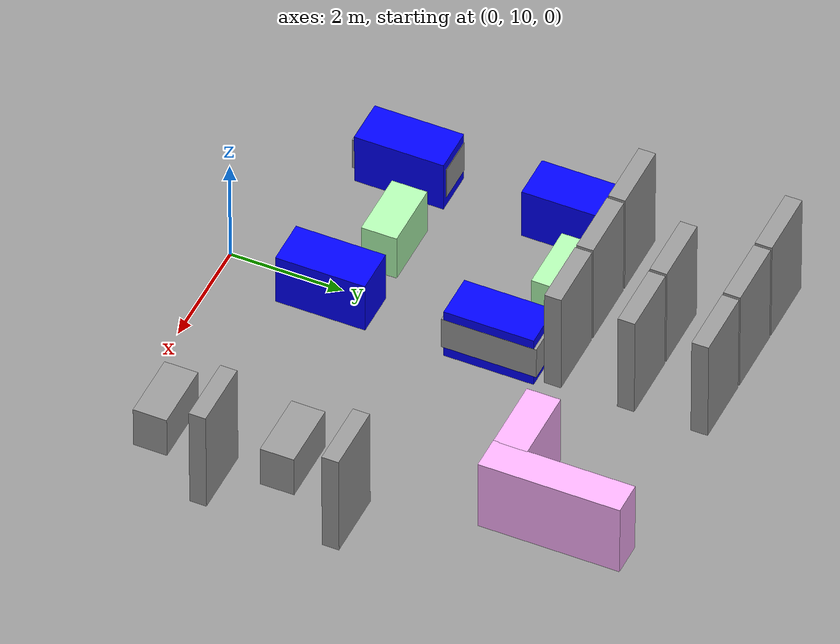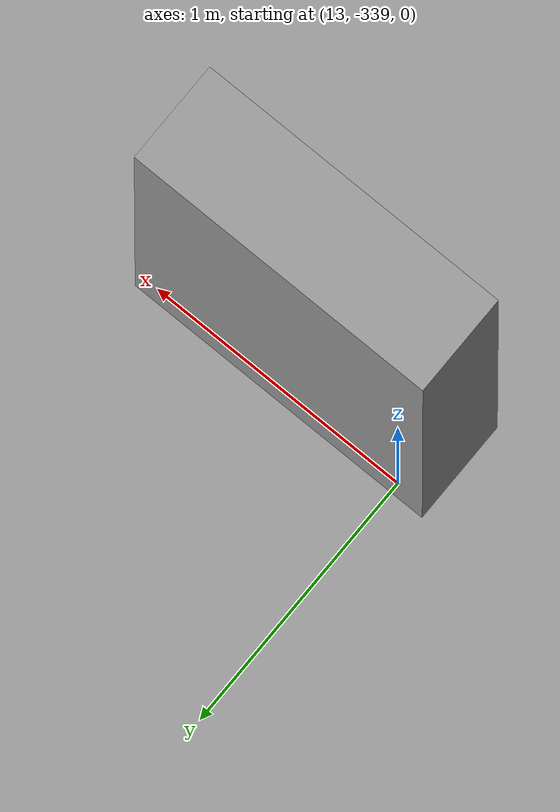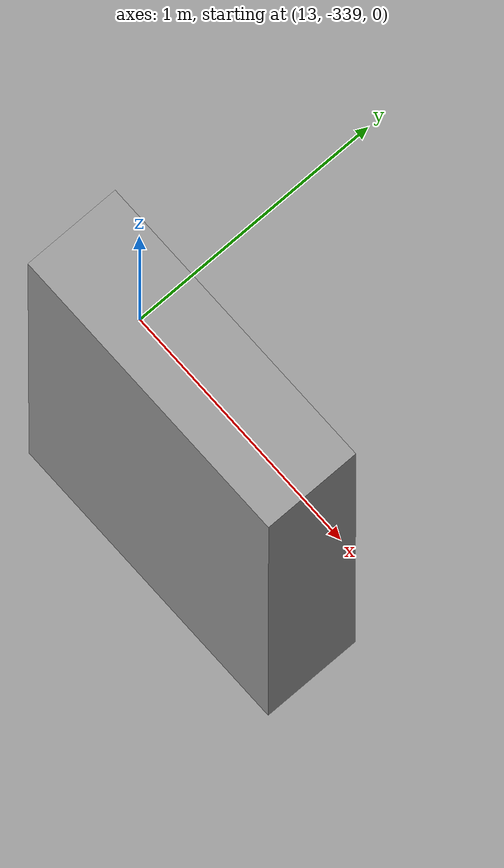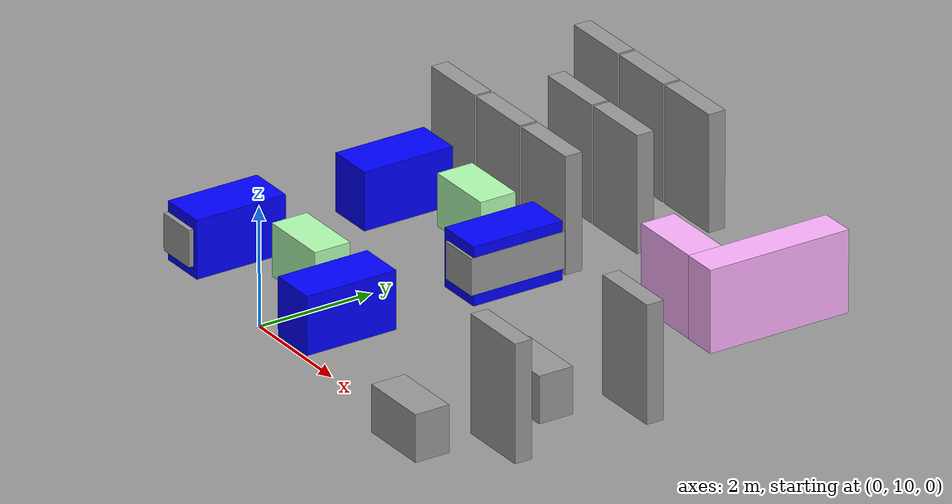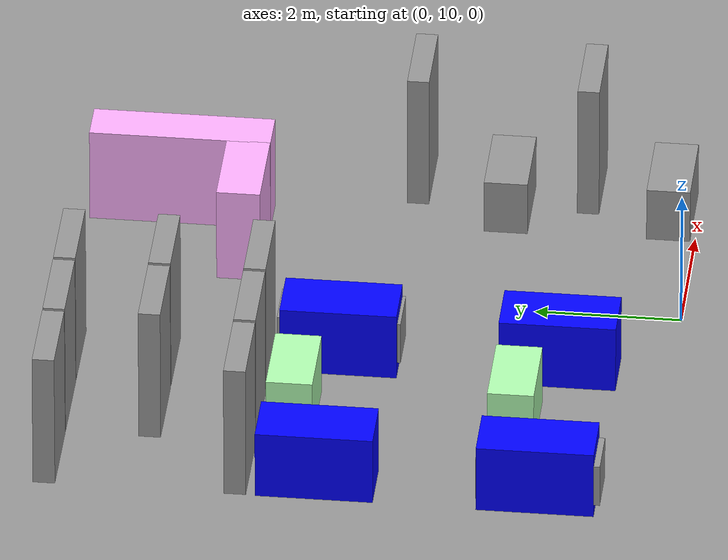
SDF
<?xml version='1.0'?>
<sdf version='1.6'>
  <model name='hospitalWithDecoration'>
    <link name='link_0'>
      <inertial>
        <mass>1.32038</mass>
        <inertia>
          <ixx>0.310098</ixx>
          <ixy>0</ixy>
          <ixz>0</ixz>
          <iyy>0.442519</iyy>
          <iyz>0</iyz>
          <izz>0.230475</izz>
        </inertia>
        <pose frame=''>0 0 0 0 -0 0</pose>
      </inertial>
      <pose frame=''>2.06742 16.2261 -0.004167 0 -0 0</pose>
      <gravity>1</gravity>
      <self_collide>0</self_collide>
      <kinematic>0</kinematic>
      <enable_wind>0</enable_wind>
      <visual name='visual'>
        <pose frame=''>0 0 0 0 -0 0</pose>
        <geometry>
          <box>
            <size>1.3 0.6 1.4</size>
          </box>
        </geometry>
        <material>
          <lighting>1</lighting>
          <script>
            <uri>file://media/materials/scripts/gazebo.material</uri>
            <name>Gazebo/Grey</name>
          </script>
          <shader type='pixel'>
            <normal_map>__default__</normal_map>
          </shader>
          <ambient>1 0 1 0</ambient>
          <diffuse>1 0.7 1 1</diffuse>
          <specular>0.01 0.01 0.01 1</specular>
          <emissive>0 0 0 1</emissive>
        </material>
        <transparency>0</transparency>
        <cast_shadows>1</cast_shadows>
      </visual>
      <collision name='collision'>
        <laser_retro>0</laser_retro>
        <max_contacts>10</max_contacts>
        <pose frame=''>0 0 0 0 -0 0</pose>
        <geometry>
          <box>
            <size>1.3 0.6 1.4</size>
          </box>
        </geometry>
        <surface>
          <friction>
            <ode>
              <mu>1</mu>
              <mu2>1</mu2>
              <fdir1>0 0 0</fdir1>
              <slip1>0</slip1>
              <slip2>0</slip2>
            </ode>
            <torsional>
              <coefficient>1</coefficient>
              <patch_radius>0</patch_radius>
              <surface_radius>0</surface_radius>
              <use_patch_radius>1</use_patch_radius>
              <ode>
                <slip>0</slip>
              </ode>
            </torsional>
          </friction>
          <bounce>
            <restitution_coefficient>0</restitution_coefficient>
            <threshold>1e+06</threshold>
          </bounce>
          <contact>
            <collide_without_contact>0</collide_without_contact>
            <collide_without_contact_bitmask>1</collide_without_contact_bitmask>
            <collide_bitmask>1</collide_bitmask>
            <ode>
              <soft_cfm>0</soft_cfm>
              <soft_erp>0.2</soft_erp>
              <kp>1e+13</kp>
              <kd>1</kd>
              <max_vel>0.01</max_vel>
              <min_depth>0</min_depth>
            </ode>
            <bullet>
              <split_impulse>1</split_impulse>
              <split_impulse_penetration_threshold>-0.01</split_impulse_penetration_threshold>
              <soft_cfm>0</soft_cfm>
              <soft_erp>0.2</soft_erp>
              <kp>1e+13</kp>
              <kd>1</kd>
            </bullet>
          </contact>
        </surface>
      </collision>
    </link>
    <link name='link_1'>
      <inertial>
        <mass>2.44409</mass>
        <inertia>
          <ixx>1.67216</ixx>
          <ixy>0</ixy>
          <ixz>0</ixz>
          <iyy>0.472523</iyy>
          <iyz>0</iyz>
          <izz>1.34629</izz>
        </inertia>
        <pose frame=''>0 0 0 0 -0 0</pose>
      </inertial>
      <pose frame=''>3.00267 17.171 -0.004167 0 -0 0</pose>
      <gravity>1</gravity>
      <self_collide>0</self_collide>
      <kinematic>0</kinematic>
      <enable_wind>0</enable_wind>
      <visual name='visual'>
        <pose frame=''>0 0 0 0 -0 0</pose>
        <geometry>
          <box>
            <size>0.6 2.5 1.4</size>
          </box>
        </geometry>
        <material>
          <lighting>1</lighting>
          <script>
            <uri>file://media/materials/scripts/gazebo.material</uri>
            <name>Gazebo/Grey</name>
          </script>
          <shader type='pixel'>
            <normal_map>__default__</normal_map>
          </shader>
          <ambient>1 0 1 0</ambient>
          <diffuse>1 0.7 1 1</diffuse>
          <specular>0.01 0.01 0.01 1</specular>
          <emissive>0 0 0 1</emissive>
        </material>
        <transparency>0</transparency>
        <cast_shadows>1</cast_shadows>
      </visual>
      <collision name='collision'>
        <laser_retro>0</laser_retro>
        <max_contacts>10</max_contacts>
        <pose frame=''>0 0 0 0 -0 0</pose>
        <geometry>
          <box>
            <size>0.6 2.5 1.4</size>
          </box>
        </geometry>
        <surface>
          <friction>
            <ode>
              <mu>1</mu>
              <mu2>1</mu2>
              <fdir1>0 0 0</fdir1>
              <slip1>0</slip1>
              <slip2>0</slip2>
            </ode>
            <torsional>
              <coefficient>1</coefficient>
              <patch_radius>0</patch_radius>
              <surface_radius>0</surface_radius>
              <use_patch_radius>1</use_patch_radius>
              <ode>
                <slip>0</slip>
              </ode>
            </torsional>
          </friction>
          <bounce>
            <restitution_coefficient>0</restitution_coefficient>
            <threshold>1e+06</threshold>
          </bounce>
          <contact>
            <collide_without_contact>0</collide_without_contact>
            <collide_without_contact_bitmask>1</collide_without_contact_bitmask>
            <collide_bitmask>1</collide_bitmask>
            <ode>
              <soft_cfm>0</soft_cfm>
              <soft_erp>0.2</soft_erp>
              <kp>1e+13</kp>
              <kd>1</kd>
              <max_vel>0.01</max_vel>
              <min_depth>0</min_depth>
            </ode>
            <bullet>
              <split_impulse>1</split_impulse>
              <split_impulse_penetration_threshold>-0.01</split_impulse_penetration_threshold>
              <soft_cfm>0</soft_cfm>
              <soft_erp>0.2</soft_erp>
              <kp>1e+13</kp>
              <kd>1</kd>
            </bullet>
          </contact>
        </surface>
      </collision>
    </link>
    <link name='link_2_clone_5'>
      <inertial>
        <mass>0.91642</mass>
        <inertia>
          <ixx>0.320278</ixx>
          <ixy>0</ixy>
          <ixz>0</ixz>
          <iyy>0.418308</iyy>
          <iyz>0</iyz>
          <izz>0.120202</izz>
        </inertia>
        <pose frame=''>0 0 0 0 -0 0</pose>
      </inertial>
      <pose frame=''>-3.18674 18.3004 0.295833 0 -0 0</pose>
      <gravity>1</gravity>
      <self_collide>0</self_collide>
      <kinematic>0</kinematic>
      <enable_wind>0</enable_wind>
      <visual name='visual'>
        <pose frame=''>0 0 0 0 -0 0</pose>
        <geometry>
          <box>
            <size>1.2 0.3 2</size>
          </box>
        </geometry>
        <material>
          <lighting>1</lighting>
          <script>
            <uri>file://media/materials/scripts/gazebo.material</uri>
            <name>Gazebo/Grey</name>
          </script>
          <shader type='pixel'>
            <normal_map>__default__</normal_map>
          </shader>
          <ambient>0.3 0.3 0.3 1</ambient>
          <diffuse>0.7 0.7 0.7 1</diffuse>
          <specular>0.01 0.01 0.01 1</specular>
          <emissive>0 0 0 1</emissive>
        </material>
        <transparency>0</transparency>
        <cast_shadows>1</cast_shadows>
      </visual>
      <visual name='ModelPreview_0::link_2_clone_5::visual_1'>
        <pose frame=''>0 0 0 0 -0 0</pose>
        <geometry>
          <box>
            <size>1.2 0.3 2</size>
          </box>
        </geometry>
        <material>
          <lighting>1</lighting>
          <script>
            <uri>file://media/materials/scripts/gazebo.material</uri>
            <name>Gazebo/Grey</name>
          </script>
          <shader type='pixel'>
            <normal_map>__default__</normal_map>
          </shader>
          <ambient>0.3 0.3 0.3 1</ambient>
          <diffuse>0.7 0.7 0.7 1</diffuse>
          <specular>0.01 0.01 0.01 1</specular>
          <emissive>0 0 0 1</emissive>
        </material>
        <transparency>0</transparency>
        <cast_shadows>1</cast_shadows>
      </visual>
      <collision name='collision'>
        <laser_retro>0</laser_retro>
        <max_contacts>10</max_contacts>
        <pose frame=''>0 0 0 0 -0 0</pose>
        <geometry>
          <box>
            <size>1.2 0.3 2</size>
          </box>
        </geometry>
        <surface>
          <friction>
            <ode>
              <mu>1</mu>
              <mu2>1</mu2>
              <fdir1>0 0 0</fdir1>
              <slip1>0</slip1>
              <slip2>0</slip2>
            </ode>
            <torsional>
              <coefficient>1</coefficient>
              <patch_radius>0</patch_radius>
              <surface_radius>0</surface_radius>
              <use_patch_radius>1</use_patch_radius>
              <ode>
                <slip>0</slip>
              </ode>
            </torsional>
          </friction>
          <bounce>
            <restitution_coefficient>0</restitution_coefficient>
            <threshold>1e+06</threshold>
          </bounce>
          <contact>
            <collide_without_contact>0</collide_without_contact>
            <collide_without_contact_bitmask>1</collide_without_contact_bitmask>
            <collide_bitmask>1</collide_bitmask>
            <ode>
              <soft_cfm>0</soft_cfm>
              <soft_erp>0.2</soft_erp>
              <kp>1e+13</kp>
              <kd>1</kd>
              <max_vel>0.01</max_vel>
              <min_depth>0</min_depth>
            </ode>
            <bullet>
              <split_impulse>1</split_impulse>
              <split_impulse_penetration_threshold>-0.01</split_impulse_penetration_threshold>
              <soft_cfm>0</soft_cfm>
              <soft_erp>0.2</soft_erp>
              <kp>1e+13</kp>
              <kd>1</kd>
            </bullet>
          </contact>
        </surface>
      </collision>
    </link>
    <link name='link_2_clone_5_clone_0'>
      <inertial>
        <mass>0.91642</mass>
        <inertia>
          <ixx>0.320278</ixx>
          <ixy>0</ixy>
          <ixz>0</ixz>
          <iyy>0.418308</iyy>
          <iyz>0</iyz>
          <izz>0.120202</izz>
        </inertia>
        <pose frame=''>0 0 0 0 -0 0</pose>
      </inertial>
      <pose frame=''>-1.93674 18.3004 0.295833 0 -0 0</pose>
      <gravity>1</gravity>
      <self_collide>0</self_collide>
      <kinematic>0</kinematic>
      <enable_wind>0</enable_wind>
      <visual name='visual'>
        <pose frame=''>0 0 0 0 -0 0</pose>
        <geometry>
          <box>
            <size>1.2 0.3 2</size>
          </box>
        </geometry>
        <material>
          <lighting>1</lighting>
          <script>
            <uri>file://media/materials/scripts/gazebo.material</uri>
            <name>Gazebo/Grey</name>
          </script>
          <shader type='pixel'>
            <normal_map>__default__</normal_map>
          </shader>
          <ambient>0.3 0.3 0.3 1</ambient>
          <diffuse>0.7 0.7 0.7 1</diffuse>
          <specular>0.01 0.01 0.01 1</specular>
          <emissive>0 0 0 1</emissive>
        </material>
        <transparency>0</transparency>
        <cast_shadows>1</cast_shadows>
      </visual>
      <visual name='visual_1'>
        <pose frame=''>0 0 0 0 -0 0</pose>
        <geometry>
          <box>
            <size>1.2 0.3 2</size>
          </box>
        </geometry>
        <material>
          <lighting>1</lighting>
          <script>
            <uri>file://media/materials/scripts/gazebo.material</uri>
            <name>Gazebo/Grey</name>
          </script>
          <shader type='pixel'>
            <normal_map>__default__</normal_map>
          </shader>
          <ambient>0.3 0.3 0.3 1</ambient>
          <diffuse>0.7 0.7 0.7 1</diffuse>
          <specular>0.01 0.01 0.01 1</specular>
          <emissive>0 0 0 1</emissive>
        </material>
        <transparency>0</transparency>
        <cast_shadows>1</cast_shadows>
      </visual>
      <collision name='collision'>
        <laser_retro>0</laser_retro>
        <max_contacts>10</max_contacts>
        <pose frame=''>0 0 0 0 -0 0</pose>
        <geometry>
          <box>
            <size>1.2 0.3 2</size>
          </box>
        </geometry>
        <surface>
          <friction>
            <ode>
              <mu>1</mu>
              <mu2>1</mu2>
              <fdir1>0 0 0</fdir1>
              <slip1>0</slip1>
              <slip2>0</slip2>
            </ode>
            <torsional>
              <coefficient>1</coefficient>
              <patch_radius>0</patch_radius>
              <surface_radius>0</surface_radius>
              <use_patch_radius>1</use_patch_radius>
              <ode>
                <slip>0</slip>
              </ode>
            </torsional>
          </friction>
          <bounce>
            <restitution_coefficient>0</restitution_coefficient>
            <threshold>1e+06</threshold>
          </bounce>
          <contact>
            <collide_without_contact>0</collide_without_contact>
            <collide_without_contact_bitmask>1</collide_without_contact_bitmask>
            <collide_bitmask>1</collide_bitmask>
            <ode>
              <soft_cfm>0</soft_cfm>
              <soft_erp>0.2</soft_erp>
              <kp>1e+13</kp>
              <kd>1</kd>
              <max_vel>0.01</max_vel>
              <min_depth>0</min_depth>
            </ode>
            <bullet>
              <split_impulse>1</split_impulse>
              <split_impulse_penetration_threshold>-0.01</split_impulse_penetration_threshold>
              <soft_cfm>0</soft_cfm>
              <soft_erp>0.2</soft_erp>
              <kp>1e+13</kp>
              <kd>1</kd>
            </bullet>
          </contact>
        </surface>
      </collision>
    </link>
    <link name='link_2_clone_5_clone_1'>
      <inertial>
        <mass>0.91642</mass>
        <inertia>
          <ixx>0.320278</ixx>
          <ixy>0</ixy>
          <ixz>0</ixz>
          <iyy>0.418308</iyy>
          <iyz>0</iyz>
          <izz>0.120202</izz>
        </inertia>
        <pose frame=''>0 0 0 0 -0 0</pose>
      </inertial>
      <pose frame=''>-0.686741 18.3004 0.295833 0 -0 0</pose>
      <gravity>1</gravity>
      <self_collide>0</self_collide>
      <kinematic>0</kinematic>
      <enable_wind>0</enable_wind>
      <visual name='visual'>
        <pose frame=''>0 0 0 0 -0 0</pose>
        <geometry>
          <box>
            <size>1.2 0.3 2</size>
          </box>
        </geometry>
        <material>
          <lighting>1</lighting>
          <script>
            <uri>file://media/materials/scripts/gazebo.material</uri>
            <name>Gazebo/Grey</name>
          </script>
          <shader type='pixel'>
            <normal_map>__default__</normal_map>
          </shader>
          <ambient>0.3 0.3 0.3 1</ambient>
          <diffuse>0.7 0.7 0.7 1</diffuse>
          <specular>0.01 0.01 0.01 1</specular>
          <emissive>0 0 0 1</emissive>
        </material>
        <transparency>0</transparency>
        <cast_shadows>1</cast_shadows>
      </visual>
      <collision name='collision'>
        <laser_retro>0</laser_retro>
        <max_contacts>10</max_contacts>
        <pose frame=''>0 0 0 0 -0 0</pose>
        <geometry>
          <box>
            <size>1.2 0.3 2</size>
          </box>
        </geometry>
        <surface>
          <friction>
            <ode>
              <mu>1</mu>
              <mu2>1</mu2>
              <fdir1>0 0 0</fdir1>
              <slip1>0</slip1>
              <slip2>0</slip2>
            </ode>
            <torsional>
              <coefficient>1</coefficient>
              <patch_radius>0</patch_radius>
              <surface_radius>0</surface_radius>
              <use_patch_radius>1</use_patch_radius>
              <ode>
                <slip>0</slip>
              </ode>
            </torsional>
          </friction>
          <bounce>
            <restitution_coefficient>0</restitution_coefficient>
            <threshold>1e+06</threshold>
          </bounce>
          <contact>
            <collide_without_contact>0</collide_without_contact>
            <collide_without_contact_bitmask>1</collide_without_contact_bitmask>
            <collide_bitmask>1</collide_bitmask>
            <ode>
              <soft_cfm>0</soft_cfm>
              <soft_erp>0.2</soft_erp>
              <kp>1e+13</kp>
              <kd>1</kd>
              <max_vel>0.01</max_vel>
              <min_depth>0</min_depth>
            </ode>
            <bullet>
              <split_impulse>1</split_impulse>
              <split_impulse_penetration_threshold>-0.01</split_impulse_penetration_threshold>
              <soft_cfm>0</soft_cfm>
              <soft_erp>0.2</soft_erp>
              <kp>1e+13</kp>
              <kd>1</kd>
            </bullet>
          </contact>
        </surface>
      </collision>
    </link>
    <link name='link_2_clone_5_clone_2'>
      <inertial>
        <mass>0.91642</mass>
        <inertia>
          <ixx>0.320278</ixx>
          <ixy>0</ixy>
          <ixz>0</ixz>
          <iyy>0.418308</iyy>
          <iyz>0</iyz>
          <izz>0.120202</izz>
        </inertia>
        <pose frame=''>0 0 0 0 -0 0</pose>
      </inertial>
      <pose frame=''>-0.686741 17.0004 0.295833 0 -0 0</pose>
      <gravity>1</gravity>
      <self_collide>0</self_collide>
      <kinematic>0</kinematic>
      <enable_wind>0</enable_wind>
      <visual name='visual_1'>
        <pose frame=''>0 0 0 0 -0 0</pose>
        <geometry>
          <box>
            <size>1.2 0.3 2</size>
          </box>
        </geometry>
        <material>
          <lighting>1</lighting>
          <script>
            <uri>file://media/materials/scripts/gazebo.material</uri>
            <name>Gazebo/Grey</name>
          </script>
          <shader type='pixel'>
            <normal_map>__default__</normal_map>
          </shader>
          <ambient>0.3 0.3 0.3 1</ambient>
          <diffuse>0.7 0.7 0.7 1</diffuse>
          <specular>0.01 0.01 0.01 1</specular>
          <emissive>0 0 0 1</emissive>
        </material>
        <transparency>0</transparency>
        <cast_shadows>1</cast_shadows>
      </visual>
      <visual name='visual'>
        <pose frame=''>0 0 0 0 -0 0</pose>
        <geometry>
          <box>
            <size>1.2 0.3 2</size>
          </box>
        </geometry>
        <material>
          <lighting>1</lighting>
          <script>
            <uri>file://media/materials/scripts/gazebo.material</uri>
            <name>Gazebo/Grey</name>
          </script>
          <shader type='pixel'>
            <normal_map>__default__</normal_map>
          </shader>
          <ambient>0.3 0.3 0.3 1</ambient>
          <diffuse>0.7 0.7 0.7 1</diffuse>
          <specular>0.01 0.01 0.01 1</specular>
          <emissive>0 0 0 1</emissive>
        </material>
        <transparency>0</transparency>
        <cast_shadows>1</cast_shadows>
      </visual>
      <collision name='collision'>
        <laser_retro>0</laser_retro>
        <max_contacts>10</max_contacts>
        <pose frame=''>0 0 0 0 -0 0</pose>
        <geometry>
          <box>
            <size>1.2 0.3 2</size>
          </box>
        </geometry>
        <surface>
          <friction>
            <ode>
              <mu>1</mu>
              <mu2>1</mu2>
              <fdir1>0 0 0</fdir1>
              <slip1>0</slip1>
              <slip2>0</slip2>
            </ode>
            <torsional>
              <coefficient>1</coefficient>
              <patch_radius>0</patch_radius>
              <surface_radius>0</surface_radius>
              <use_patch_radius>1</use_patch_radius>
              <ode>
                <slip>0</slip>
              </ode>
            </torsional>
          </friction>
          <bounce>
            <restitution_coefficient>0</restitution_coefficient>
            <threshold>1e+06</threshold>
          </bounce>
          <contact>
            <collide_without_contact>0</collide_without_contact>
            <collide_without_contact_bitmask>1</collide_without_contact_bitmask>
            <collide_bitmask>1</collide_bitmask>
            <ode>
              <soft_cfm>0</soft_cfm>
              <soft_erp>0.2</soft_erp>
              <kp>1e+13</kp>
              <kd>1</kd>
              <max_vel>0.01</max_vel>
              <min_depth>0</min_depth>
            </ode>
            <bullet>
              <split_impulse>1</split_impulse>
              <split_impulse_penetration_threshold>-0.01</split_impulse_penetration_threshold>
              <soft_cfm>0</soft_cfm>
              <soft_erp>0.2</soft_erp>
              <kp>1e+13</kp>
              <kd>1</kd>
            </bullet>
          </contact>
        </surface>
      </collision>
    </link>
    <link name='link_2_clone_5_clone_2_clone'>
      <inertial>
        <mass>0.91642</mass>
        <inertia>
          <ixx>0.320278</ixx>
          <ixy>0</ixy>
          <ixz>0</ixz>
          <iyy>0.418308</iyy>
          <iyz>0</iyz>
          <izz>0.120202</izz>
        </inertia>
        <pose frame=''>0 0 0 0 -0 0</pose>
      </inertial>
      <pose frame=''>4.13354 13.9745 0.295833 0 -0 0</pose>
      <gravity>1</gravity>
      <self_collide>0</self_collide>
      <kinematic>0</kinematic>
      <enable_wind>0</enable_wind>
      <visual name='visual'>
        <pose frame=''>0 0 0 0 -0 0</pose>
        <geometry>
          <box>
            <size>1.2 0.3 2</size>
          </box>
        </geometry>
        <material>
          <lighting>1</lighting>
          <script>
            <uri>file://media/materials/scripts/gazebo.material</uri>
            <name>Gazebo/Grey</name>
          </script>
          <shader type='pixel'>
            <normal_map>__default__</normal_map>
          </shader>
          <ambient>0.3 0.3 0.3 1</ambient>
          <diffuse>0.7 0.7 0.7 1</diffuse>
          <specular>0.01 0.01 0.01 1</specular>
          <emissive>0 0 0 1</emissive>
        </material>
        <transparency>0</transparency>
        <cast_shadows>1</cast_shadows>
      </visual>
      <visual name='visual_1'>
        <pose frame=''>0 0 0 0 -0 0</pose>
        <geometry>
          <box>
            <size>1.2 0.3 2</size>
          </box>
        </geometry>
        <material>
          <lighting>1</lighting>
          <script>
            <uri>file://media/materials/scripts/gazebo.material</uri>
            <name>Gazebo/Grey</name>
          </script>
          <shader type='pixel'>
            <normal_map>__default__</normal_map>
          </shader>
          <ambient>0.3 0.3 0.3 1</ambient>
          <diffuse>0.7 0.7 0.7 1</diffuse>
          <specular>0.01 0.01 0.01 1</specular>
          <emissive>0 0 0 1</emissive>
        </material>
        <transparency>0</transparency>
        <cast_shadows>1</cast_shadows>
      </visual>
      <collision name='collision'>
        <laser_retro>0</laser_retro>
        <max_contacts>10</max_contacts>
        <pose frame=''>0 0 0 0 -0 0</pose>
        <geometry>
          <box>
            <size>1.2 0.3 2</size>
          </box>
        </geometry>
        <surface>
          <friction>
            <ode>
              <mu>1</mu>
              <mu2>1</mu2>
              <fdir1>0 0 0</fdir1>
              <slip1>0</slip1>
              <slip2>0</slip2>
            </ode>
            <torsional>
              <coefficient>1</coefficient>
              <patch_radius>0</patch_radius>
              <surface_radius>0</surface_radius>
              <use_patch_radius>1</use_patch_radius>
              <ode>
                <slip>0</slip>
              </ode>
            </torsional>
          </friction>
          <bounce>
            <restitution_coefficient>0</restitution_coefficient>
            <threshold>1e+06</threshold>
          </bounce>
          <contact>
            <collide_without_contact>0</collide_without_contact>
            <collide_without_contact_bitmask>1</collide_without_contact_bitmask>
            <collide_bitmask>1</collide_bitmask>
            <ode>
              <soft_cfm>0</soft_cfm>
              <soft_erp>0.2</soft_erp>
              <kp>1e+13</kp>
              <kd>1</kd>
              <max_vel>0.01</max_vel>
              <min_depth>0</min_depth>
            </ode>
            <bullet>
              <split_impulse>1</split_impulse>
              <split_impulse_penetration_threshold>-0.01</split_impulse_penetration_threshold>
              <soft_cfm>0</soft_cfm>
              <soft_erp>0.2</soft_erp>
              <kp>1e+13</kp>
              <kd>1</kd>
            </bullet>
          </contact>
        </surface>
      </collision>
    </link>
    <link name='link_2_clone_5_clone_2_clone_0'>
      <inertial>
        <mass>0.91642</mass>
        <inertia>
          <ixx>0.320278</ixx>
          <ixy>0</ixy>
          <ixz>0</ixz>
          <iyy>0.418308</iyy>
          <iyz>0</iyz>
          <izz>0.120202</izz>
        </inertia>
        <pose frame=''>0 0 0 0 -0 0</pose>
      </inertial>
      <pose frame=''>4.12688 11.6246 0.295833 0 -0 0</pose>
      <gravity>1</gravity>
      <self_collide>0</self_collide>
      <kinematic>0</kinematic>
      <enable_wind>0</enable_wind>
      <visual name='visual_1'>
        <pose frame=''>0 0 0 0 -0 0</pose>
        <geometry>
          <box>
            <size>1.2 0.3 2</size>
          </box>
        </geometry>
        <material>
          <lighting>1</lighting>
          <script>
            <uri>file://media/materials/scripts/gazebo.material</uri>
            <name>Gazebo/Grey</name>
          </script>
          <shader type='pixel'>
            <normal_map>__default__</normal_map>
          </shader>
          <ambient>0.3 0.3 0.3 1</ambient>
          <diffuse>0.7 0.7 0.7 1</diffuse>
          <specular>0.01 0.01 0.01 1</specular>
          <emissive>0 0 0 1</emissive>
        </material>
        <transparency>0</transparency>
        <cast_shadows>1</cast_shadows>
      </visual>
      <visual name='visual'>
        <pose frame=''>0 0 0 0 -0 0</pose>
        <geometry>
          <box>
            <size>1.2 0.3 2</size>
          </box>
        </geometry>
        <material>
          <lighting>1</lighting>
          <script>
            <uri>file://media/materials/scripts/gazebo.material</uri>
            <name>Gazebo/Grey</name>
          </script>
          <shader type='pixel'>
            <normal_map>__default__</normal_map>
          </shader>
          <ambient>0.3 0.3 0.3 1</ambient>
          <diffuse>0.7 0.7 0.7 1</diffuse>
          <specular>0.01 0.01 0.01 1</specular>
          <emissive>0 0 0 1</emissive>
        </material>
        <transparency>0</transparency>
        <cast_shadows>1</cast_shadows>
      </visual>
      <collision name='collision'>
        <laser_retro>0</laser_retro>
        <max_contacts>10</max_contacts>
        <pose frame=''>0 0 0 0 -0 0</pose>
        <geometry>
          <box>
            <size>1.2 0.3 2</size>
          </box>
        </geometry>
        <surface>
          <friction>
            <ode>
              <mu>1</mu>
              <mu2>1</mu2>
              <fdir1>0 0 0</fdir1>
              <slip1>0</slip1>
              <slip2>0</slip2>
            </ode>
            <torsional>
              <coefficient>1</coefficient>
              <patch_radius>0</patch_radius>
              <surface_radius>0</surface_radius>
              <use_patch_radius>1</use_patch_radius>
              <ode>
                <slip>0</slip>
              </ode>
            </torsional>
          </friction>
          <bounce>
            <restitution_coefficient>0</restitution_coefficient>
            <threshold>1e+06</threshold>
          </bounce>
          <contact>
            <collide_without_contact>0</collide_without_contact>
            <collide_without_contact_bitmask>1</collide_without_contact_bitmask>
            <collide_bitmask>1</collide_bitmask>
            <ode>
              <soft_cfm>0</soft_cfm>
              <soft_erp>0.2</soft_erp>
              <kp>1e+13</kp>
              <kd>1</kd>
              <max_vel>0.01</max_vel>
              <min_depth>0</min_depth>
            </ode>
            <bullet>
              <split_impulse>1</split_impulse>
              <split_impulse_penetration_threshold>-0.01</split_impulse_penetration_threshold>
              <soft_cfm>0</soft_cfm>
              <soft_erp>0.2</soft_erp>
              <kp>1e+13</kp>
              <kd>1</kd>
            </bullet>
          </contact>
        </surface>
      </collision>
    </link>
    <link name='link_2_clone_5_clone_3'>
      <inertial>
        <mass>0.91642</mass>
        <inertia>
          <ixx>0.320278</ixx>
          <ixy>0</ixy>
          <ixz>0</ixz>
          <iyy>0.418308</iyy>
          <iyz>0</iyz>
          <izz>0.120202</izz>
        </inertia>
        <pose frame=''>0 0 0 0 -0 0</pose>
      </inertial>
      <pose frame=''>-1.93674 17.0004 0.295833 0 -0 0</pose>
      <gravity>1</gravity>
      <self_collide>0</self_collide>
      <kinematic>0</kinematic>
      <enable_wind>0</enable_wind>
      <visual name='visual_1'>
        <pose frame=''>0 0 0 0 -0 0</pose>
        <geometry>
          <box>
            <size>1.2 0.3 2</size>
          </box>
        </geometry>
        <material>
          <lighting>1</lighting>
          <script>
            <uri>file://media/materials/scripts/gazebo.material</uri>
            <name>Gazebo/Grey</name>
          </script>
          <shader type='pixel'>
            <normal_map>__default__</normal_map>
          </shader>
          <ambient>0.3 0.3 0.3 1</ambient>
          <diffuse>0.7 0.7 0.7 1</diffuse>
          <specular>0.01 0.01 0.01 1</specular>
          <emissive>0 0 0 1</emissive>
        </material>
        <transparency>0</transparency>
        <cast_shadows>1</cast_shadows>
      </visual>
      <visual name='visual'>
        <pose frame=''>0 0 0 0 -0 0</pose>
        <geometry>
          <box>
            <size>1.2 0.3 2</size>
          </box>
        </geometry>
        <material>
          <lighting>1</lighting>
          <script>
            <uri>file://media/materials/scripts/gazebo.material</uri>
            <name>Gazebo/Grey</name>
          </script>
          <shader type='pixel'>
            <normal_map>__default__</normal_map>
          </shader>
          <ambient>0.3 0.3 0.3 1</ambient>
          <diffuse>0.7 0.7 0.7 1</diffuse>
          <specular>0.01 0.01 0.01 1</specular>
          <emissive>0 0 0 1</emissive>
        </material>
        <transparency>0</transparency>
        <cast_shadows>1</cast_shadows>
      </visual>
      <collision name='collision'>
        <laser_retro>0</laser_retro>
        <max_contacts>10</max_contacts>
        <pose frame=''>0 0 0 0 -0 0</pose>
        <geometry>
          <box>
            <size>1.2 0.3 2</size>
          </box>
        </geometry>
        <surface>
          <friction>
            <ode>
              <mu>1</mu>
              <mu2>1</mu2>
              <fdir1>0 0 0</fdir1>
              <slip1>0</slip1>
              <slip2>0</slip2>
            </ode>
            <torsional>
              <coefficient>1</coefficient>
              <patch_radius>0</patch_radius>
              <surface_radius>0</surface_radius>
              <use_patch_radius>1</use_patch_radius>
              <ode>
                <slip>0</slip>
              </ode>
            </torsional>
          </friction>
          <bounce>
            <restitution_coefficient>0</restitution_coefficient>
            <threshold>1e+06</threshold>
          </bounce>
          <contact>
            <collide_without_contact>0</collide_without_contact>
            <collide_without_contact_bitmask>1</collide_without_contact_bitmask>
            <collide_bitmask>1</collide_bitmask>
            <ode>
              <soft_cfm>0</soft_cfm>
              <soft_erp>0.2</soft_erp>
              <kp>1e+13</kp>
              <kd>1</kd>
              <max_vel>0.01</max_vel>
              <min_depth>0</min_depth>
            </ode>
            <bullet>
              <split_impulse>1</split_impulse>
              <split_impulse_penetration_threshold>-0.01</split_impulse_penetration_threshold>
              <soft_cfm>0</soft_cfm>
              <soft_erp>0.2</soft_erp>
              <kp>1e+13</kp>
              <kd>1</kd>
            </bullet>
          </contact>
        </surface>
      </collision>
    </link>
    <link name='link_2_clone_5_clone_4'>
      <inertial>
        <mass>0.91642</mass>
        <inertia>
          <ixx>0.320278</ixx>
          <ixy>0</ixy>
          <ixz>0</ixz>
          <iyy>0.418308</iyy>
          <iyz>0</iyz>
          <izz>0.120202</izz>
        </inertia>
        <pose frame=''>0 0 0 0 -0 0</pose>
      </inertial>
      <pose frame=''>-0.686741 15.7004 0.295833 0 -0 0</pose>
      <gravity>1</gravity>
      <self_collide>0</self_collide>
      <kinematic>0</kinematic>
      <enable_wind>0</enable_wind>
      <visual name='visual'>
        <pose frame=''>0 0 0 0 -0 0</pose>
        <geometry>
          <box>
            <size>1.2 0.3 2</size>
          </box>
        </geometry>
        <material>
          <lighting>1</lighting>
          <script>
            <uri>file://media/materials/scripts/gazebo.material</uri>
            <name>Gazebo/Grey</name>
          </script>
          <shader type='pixel'>
            <normal_map>__default__</normal_map>
          </shader>
          <ambient>0.3 0.3 0.3 1</ambient>
          <diffuse>0.7 0.7 0.7 1</diffuse>
          <specular>0.01 0.01 0.01 1</specular>
          <emissive>0 0 0 1</emissive>
        </material>
        <transparency>0</transparency>
        <cast_shadows>1</cast_shadows>
      </visual>
      <visual name='visual_1'>
        <pose frame=''>0 0 0 0 -0 0</pose>
        <geometry>
          <box>
            <size>1.2 0.3 2</size>
          </box>
        </geometry>
        <material>
          <lighting>1</lighting>
          <script>
            <uri>file://media/materials/scripts/gazebo.material</uri>
            <name>Gazebo/Grey</name>
          </script>
          <shader type='pixel'>
            <normal_map>__default__</normal_map>
          </shader>
          <ambient>0.3 0.3 0.3 1</ambient>
          <diffuse>0.7 0.7 0.7 1</diffuse>
          <specular>0.01 0.01 0.01 1</specular>
          <emissive>0 0 0 1</emissive>
        </material>
        <transparency>0</transparency>
        <cast_shadows>1</cast_shadows>
      </visual>
      <collision name='collision'>
        <laser_retro>0</laser_retro>
        <max_contacts>10</max_contacts>
        <pose frame=''>0 0 0 0 -0 0</pose>
        <geometry>
          <box>
            <size>1.2 0.3 2</size>
          </box>
        </geometry>
        <surface>
          <friction>
            <ode>
              <mu>1</mu>
              <mu2>1</mu2>
              <fdir1>0 0 0</fdir1>
              <slip1>0</slip1>
              <slip2>0</slip2>
            </ode>
            <torsional>
              <coefficient>1</coefficient>
              <patch_radius>0</patch_radius>
              <surface_radius>0</surface_radius>
              <use_patch_radius>1</use_patch_radius>
              <ode>
                <slip>0</slip>
              </ode>
            </torsional>
          </friction>
          <bounce>
            <restitution_coefficient>0</restitution_coefficient>
            <threshold>1e+06</threshold>
          </bounce>
          <contact>
            <collide_without_contact>0</collide_without_contact>
            <collide_without_contact_bitmask>1</collide_without_contact_bitmask>
            <collide_bitmask>1</collide_bitmask>
            <ode>
              <soft_cfm>0</soft_cfm>
              <soft_erp>0.2</soft_erp>
              <kp>1e+13</kp>
              <kd>1</kd>
              <max_vel>0.01</max_vel>
              <min_depth>0</min_depth>
            </ode>
            <bullet>
              <split_impulse>1</split_impulse>
              <split_impulse_penetration_threshold>-0.01</split_impulse_penetration_threshold>
              <soft_cfm>0</soft_cfm>
              <soft_erp>0.2</soft_erp>
              <kp>1e+13</kp>
              <kd>1</kd>
            </bullet>
          </contact>
        </surface>
      </collision>
    </link>
    <link name='link_2_clone_5_clone_5'>
      <inertial>
        <mass>0.91642</mass>
        <inertia>
          <ixx>0.320278</ixx>
          <ixy>0</ixy>
          <ixz>0</ixz>
          <iyy>0.418308</iyy>
          <iyz>0</iyz>
          <izz>0.120202</izz>
        </inertia>
        <pose frame=''>1.95 0.2 1 0 -0 0</pose>
      </inertial>
      <pose frame=''>-1.93674 15.7004 0.295833 0 -0 0</pose>
      <gravity>1</gravity>
      <self_collide>0</self_collide>
      <kinematic>0</kinematic>
      <enable_wind>0</enable_wind>
      <visual name='visual'>
        <pose frame=''>0 0 0 0 -0 0</pose>
        <geometry>
          <box>
            <size>1.2 0.3 2</size>
          </box>
        </geometry>
        <material>
          <lighting>1</lighting>
          <script>
            <uri>file://media/materials/scripts/gazebo.material</uri>
            <name>Gazebo/Grey</name>
          </script>
          <shader type='pixel'>
            <normal_map>__default__</normal_map>
          </shader>
          <ambient>0.3 0.3 0.3 1</ambient>
          <diffuse>0.7 0.7 0.7 1</diffuse>
          <specular>0.01 0.01 0.01 1</specular>
          <emissive>0 0 0 1</emissive>
        </material>
        <transparency>0</transparency>
        <cast_shadows>1</cast_shadows>
      </visual>
      <visual name='visual_1'>
        <pose frame=''>0 0 0 0 -0 0</pose>
        <geometry>
          <box>
            <size>1.2 0.3 2</size>
          </box>
        </geometry>
        <material>
          <lighting>1</lighting>
          <script>
            <uri>file://media/materials/scripts/gazebo.material</uri>
            <name>Gazebo/Grey</name>
          </script>
          <shader type='pixel'>
            <normal_map>__default__</normal_map>
          </shader>
          <ambient>0.3 0.3 0.3 1</ambient>
          <diffuse>0.7 0.7 0.7 1</diffuse>
          <specular>0.01 0.01 0.01 1</specular>
          <emissive>0 0 0 1</emissive>
        </material>
        <transparency>0</transparency>
        <cast_shadows>1</cast_shadows>
      </visual>
      <collision name='collision'>
        <laser_retro>0</laser_retro>
        <max_contacts>10</max_contacts>
        <pose frame=''>0 0 0 0 -0 0</pose>
        <geometry>
          <box>
            <size>1.2 0.32 2.02</size>
          </box>
        </geometry>
        <surface>
          <friction>
            <ode>
              <mu>1</mu>
              <mu2>1</mu2>
              <fdir1>0 0 0</fdir1>
              <slip1>0</slip1>
              <slip2>0</slip2>
            </ode>
            <torsional>
              <coefficient>1</coefficient>
              <patch_radius>0</patch_radius>
              <surface_radius>0</surface_radius>
              <use_patch_radius>1</use_patch_radius>
              <ode>
                <slip>0</slip>
              </ode>
            </torsional>
          </friction>
          <bounce>
            <restitution_coefficient>0</restitution_coefficient>
            <threshold>1e+06</threshold>
          </bounce>
          <contact>
            <collide_without_contact>0</collide_without_contact>
            <collide_without_contact_bitmask>1</collide_without_contact_bitmask>
            <collide_bitmask>1</collide_bitmask>
            <ode>
              <soft_cfm>0</soft_cfm>
              <soft_erp>0.2</soft_erp>
              <kp>1e+13</kp>
              <kd>1</kd>
              <max_vel>0.01</max_vel>
              <min_depth>0</min_depth>
            </ode>
            <bullet>
              <split_impulse>1</split_impulse>
              <split_impulse_penetration_threshold>-0.01</split_impulse_penetration_threshold>
              <soft_cfm>0</soft_cfm>
              <soft_erp>0.2</soft_erp>
              <kp>1e+13</kp>
              <kd>1</kd>
            </bullet>
          </contact>
        </surface>
      </collision>
    </link>
    <link name='link_2_clone_5_clone_6'>
      <inertial>
        <mass>0.91642</mass>
        <inertia>
          <ixx>0.320278</ixx>
          <ixy>0</ixy>
          <ixz>0</ixz>
          <iyy>0.418308</iyy>
          <iyz>0</iyz>
          <izz>0.120202</izz>
        </inertia>
        <pose frame=''>0 0 0 0 -0 0</pose>
      </inertial>
      <pose frame=''>-3.18674 15.7004 0.295833 0 -0 0</pose>
      <gravity>1</gravity>
      <self_collide>0</self_collide>
      <kinematic>0</kinematic>
      <enable_wind>0</enable_wind>
      <visual name='visual'>
        <pose frame=''>0 0 0 0 -0 0</pose>
        <geometry>
          <box>
            <size>1.2 0.3 2</size>
          </box>
        </geometry>
        <material>
          <lighting>1</lighting>
          <script>
            <uri>file://media/materials/scripts/gazebo.material</uri>
            <name>Gazebo/Grey</name>
          </script>
          <shader type='pixel'>
            <normal_map>__default__</normal_map>
          </shader>
          <ambient>0.3 0.3 0.3 1</ambient>
          <diffuse>0.7 0.7 0.7 1</diffuse>
          <specular>0.01 0.01 0.01 1</specular>
          <emissive>0 0 0 1</emissive>
        </material>
        <transparency>0</transparency>
        <cast_shadows>1</cast_shadows>
      </visual>
      <visual name='visual_1'>
        <pose frame=''>0 0 0 0 -0 0</pose>
        <geometry>
          <box>
            <size>1.2 0.3 2</size>
          </box>
        </geometry>
        <material>
          <lighting>1</lighting>
          <script>
            <uri>file://media/materials/scripts/gazebo.material</uri>
            <name>Gazebo/Grey</name>
          </script>
          <shader type='pixel'>
            <normal_map>__default__</normal_map>
          </shader>
          <ambient>0.3 0.3 0.3 1</ambient>
          <diffuse>0.7 0.7 0.7 1</diffuse>
          <specular>0.01 0.01 0.01 1</specular>
          <emissive>0 0 0 1</emissive>
        </material>
        <transparency>0</transparency>
        <cast_shadows>1</cast_shadows>
      </visual>
      <collision name='collision'>
        <laser_retro>0</laser_retro>
        <max_contacts>10</max_contacts>
        <pose frame=''>0 0 0 0 -0 0</pose>
        <geometry>
          <box>
            <size>1.2 0.3 2</size>
          </box>
        </geometry>
        <surface>
          <friction>
            <ode>
              <mu>1</mu>
              <mu2>1</mu2>
              <fdir1>0 0 0</fdir1>
              <slip1>0</slip1>
              <slip2>0</slip2>
            </ode>
            <torsional>
              <coefficient>1</coefficient>
              <patch_radius>0</patch_radius>
              <surface_radius>0</surface_radius>
              <use_patch_radius>1</use_patch_radius>
              <ode>
                <slip>0</slip>
              </ode>
            </torsional>
          </friction>
          <bounce>
            <restitution_coefficient>0</restitution_coefficient>
            <threshold>1e+06</threshold>
          </bounce>
          <contact>
            <collide_without_contact>0</collide_without_contact>
            <collide_without_contact_bitmask>1</collide_without_contact_bitmask>
            <collide_bitmask>1</collide_bitmask>
            <ode>
              <soft_cfm>0</soft_cfm>
              <soft_erp>0.2</soft_erp>
              <kp>1e+13</kp>
              <kd>1</kd>
              <max_vel>0.01</max_vel>
              <min_depth>0</min_depth>
            </ode>
            <bullet>
              <split_impulse>1</split_impulse>
              <split_impulse_penetration_threshold>-0.01</split_impulse_penetration_threshold>
              <soft_cfm>0</soft_cfm>
              <soft_erp>0.2</soft_erp>
              <kp>1e+13</kp>
              <kd>1</kd>
            </bullet>
          </contact>
        </surface>
      </collision>
    </link>
    <link name='link_2_clone_clone_0'>
      <inertial>
        <mass>1.6162</mass>
        <inertia>
          <ixx>1.71556</ixx>
          <ixy>0</ixy>
          <ixz>0</ixz>
          <iyy>1.88844</iyy>
          <iyz>0</iyz>
          <izz>0.211988</izz>
        </inertia>
        <pose frame=''>0 0 0 0 -0 0</pose>
      </inertial>
      <pose frame=''>13.5476 -339.253 -0.204167 0 -0 0</pose>
      <visual name='visual'>
        <pose frame=''>0 0 0 0 -0 0</pose>
        <geometry>
          <box>
            <size>1.19533 0.380996 3.5486</size>
          </box>
        </geometry>
        <material>
          <lighting>1</lighting>
          <script>
            <uri>file://media/materials/scripts/gazebo.material</uri>
            <name>Gazebo/Grey</name>
          </script>
          <shader type='pixel'/>
        </material>
        <transparency>0</transparency>
        <cast_shadows>1</cast_shadows>
      </visual>
      <collision name='collision'>
        <laser_retro>0</laser_retro>
        <max_contacts>10</max_contacts>
        <pose frame=''>0 0 0 0 -0 0</pose>
        <geometry>
          <box>
            <size>1.19533 0.380996 3.5486</size>
          </box>
        </geometry>
        <surface>
          <friction>
            <ode>
              <mu>1</mu>
              <mu2>1</mu2>
              <fdir1>0 0 0</fdir1>
              <slip1>0</slip1>
              <slip2>0</slip2>
            </ode>
            <torsional>
              <coefficient>1</coefficient>
              <patch_radius>0</patch_radius>
              <surface_radius>0</surface_radius>
              <use_patch_radius>1</use_patch_radius>
              <ode>
                <slip>0</slip>
              </ode>
            </torsional>
          </friction>
          <bounce>
            <restitution_coefficient>0</restitution_coefficient>
            <threshold>1e+06</threshold>
          </bounce>
          <contact>
            <collide_without_contact>0</collide_without_contact>
            <collide_without_contact_bitmask>1</collide_without_contact_bitmask>
            <collide_bitmask>1</collide_bitmask>
            <ode>
              <soft_cfm>0</soft_cfm>
              <soft_erp>0.2</soft_erp>
              <kp>1e+13</kp>
              <kd>1</kd>
              <max_vel>0.01</max_vel>
              <min_depth>0</min_depth>
            </ode>
            <bullet>
              <split_impulse>1</split_impulse>
              <split_impulse_penetration_threshold>-0.01</split_impulse_penetration_threshold>
              <soft_cfm>0</soft_cfm>
              <soft_erp>0.2</soft_erp>
              <kp>1e+13</kp>
              <kd>1</kd>
            </bullet>
          </contact>
        </surface>
      </collision>
    </link>
    <link name='link_2_clone_clone_clone_0_clone'>
      <inertial>
        <mass>684.4</mass>
        <inertia>
          <ixx>185.873</ixx>
          <ixy>0</ixy>
          <ixz>0</ixz>
          <iyy>50.6679</iyy>
          <iyz>0</iyz>
          <izz>191.332</izz>
        </inertia>
        <pose frame=''>0 0 0 0 -0 0</pose>
      </inertial>
      <pose frame=''>-3.46295 11.5811 -0.204167 0 -0 0</pose>
      <gravity>1</gravity>
      <self_collide>0</self_collide>
      <kinematic>0</kinematic>
      <enable_wind>0</enable_wind>
      <visual name='visual'>
        <pose frame=''>0 0 0 0 -0 0</pose>
        <geometry>
          <box>
            <size>0.701464 1.69195 0.629555</size>
          </box>
        </geometry>
        <material>
          <lighting>1</lighting>
          <script>
            <uri>file://media/materials/scripts/gazebo.material</uri>
            <name>Gazebo/Grey</name>
          </script>
          <shader type='pixel'>
            <normal_map>__default__</normal_map>
          </shader>
          <ambient>0.3 0.3 0.3 1</ambient>
          <diffuse>0.7 0.7 0.7 1</diffuse>
          <specular>0.01 0.01 0.01 1</specular>
          <emissive>0 0 0 1</emissive>
        </material>
        <transparency>0</transparency>
        <cast_shadows>1</cast_shadows>
      </visual>
      <collision name='collision'>
        <laser_retro>0</laser_retro>
        <max_contacts>10</max_contacts>
        <pose frame=''>0 0 0 0 -0 0</pose>
        <geometry>
          <box>
            <size>0.701464 1.69195 0.629555</size>
          </box>
        </geometry>
        <surface>
          <friction>
            <ode>
              <mu>1</mu>
              <mu2>1</mu2>
              <fdir1>0 0 0</fdir1>
              <slip1>0</slip1>
              <slip2>0</slip2>
            </ode>
            <torsional>
              <coefficient>1</coefficient>
              <patch_radius>0</patch_radius>
              <surface_radius>0</surface_radius>
              <use_patch_radius>1</use_patch_radius>
              <ode>
                <slip>0</slip>
              </ode>
            </torsional>
          </friction>
          <bounce>
            <restitution_coefficient>0</restitution_coefficient>
            <threshold>1e+06</threshold>
          </bounce>
          <contact>
            <collide_without_contact>0</collide_without_contact>
            <collide_without_contact_bitmask>1</collide_without_contact_bitmask>
            <collide_bitmask>1</collide_bitmask>
            <ode>
              <soft_cfm>0</soft_cfm>
              <soft_erp>0.2</soft_erp>
              <kp>1e+13</kp>
              <kd>1</kd>
              <max_vel>0.01</max_vel>
              <min_depth>0</min_depth>
            </ode>
            <bullet>
              <split_impulse>1</split_impulse>
              <split_impulse_penetration_threshold>-0.01</split_impulse_penetration_threshold>
              <soft_cfm>0</soft_cfm>
              <soft_erp>0.2</soft_erp>
              <kp>1e+13</kp>
              <kd>1</kd>
            </bullet>
          </contact>
        </surface>
      </collision>
    </link>
    <link name='link_2_clone_clone_clone_0_clone_0'>
      <inertial>
        <mass>684.4</mass>
        <inertia>
          <ixx>185.873</ixx>
          <ixy>0</ixy>
          <ixz>0</ixz>
          <iyy>50.6679</iyy>
          <iyz>0</iyz>
          <izz>191.332</izz>
        </inertia>
        <pose frame=''>0 0 0 0 -0 0</pose>
      </inertial>
      <pose frame=''>-0.320598 14.6198 -0.204167 0 -0 0</pose>
      <gravity>1</gravity>
      <self_collide>0</self_collide>
      <kinematic>0</kinematic>
      <enable_wind>0</enable_wind>
      <visual name='visual'>
        <pose frame=''>0 0 0 0 -0 0</pose>
        <geometry>
          <box>
            <size>0.701464 1.69195 0.629555</size>
          </box>
        </geometry>
        <material>
          <lighting>1</lighting>
          <script>
            <uri>file://media/materials/scripts/gazebo.material</uri>
            <name>Gazebo/Grey</name>
          </script>
          <shader type='pixel'>
            <normal_map>__default__</normal_map>
          </shader>
          <ambient>0.3 0.3 0.3 1</ambient>
          <diffuse>0.7 0.7 0.7 1</diffuse>
          <specular>0.01 0.01 0.01 1</specular>
          <emissive>0 0 0 1</emissive>
        </material>
        <transparency>0</transparency>
        <cast_shadows>1</cast_shadows>
      </visual>
      <collision name='collision'>
        <laser_retro>0</laser_retro>
        <max_contacts>10</max_contacts>
        <pose frame=''>0 0 0 0 -0 0</pose>
        <geometry>
          <box>
            <size>0.701464 1.69195 0.629555</size>
          </box>
        </geometry>
        <surface>
          <friction>
            <ode>
              <mu>1</mu>
              <mu2>1</mu2>
              <fdir1>0 0 0</fdir1>
              <slip1>0</slip1>
              <slip2>0</slip2>
            </ode>
            <torsional>
              <coefficient>1</coefficient>
              <patch_radius>0</patch_radius>
              <surface_radius>0</surface_radius>
              <use_patch_radius>1</use_patch_radius>
              <ode>
                <slip>0</slip>
              </ode>
            </torsional>
          </friction>
          <bounce>
            <restitution_coefficient>0</restitution_coefficient>
            <threshold>1e+06</threshold>
          </bounce>
          <contact>
            <collide_without_contact>0</collide_without_contact>
            <collide_without_contact_bitmask>1</collide_without_contact_bitmask>
            <collide_bitmask>1</collide_bitmask>
            <ode>
              <soft_cfm>0</soft_cfm>
              <soft_erp>0.2</soft_erp>
              <kp>1e+13</kp>
              <kd>1</kd>
              <max_vel>0.01</max_vel>
              <min_depth>0</min_depth>
            </ode>
            <bullet>
              <split_impulse>1</split_impulse>
              <split_impulse_penetration_threshold>-0.01</split_impulse_penetration_threshold>
              <soft_cfm>0</soft_cfm>
              <soft_erp>0.2</soft_erp>
              <kp>1e+13</kp>
              <kd>1</kd>
            </bullet>
          </contact>
        </surface>
      </collision>
    </link>
    <link name='link_2_clone_clone_clone_clone'>
      <inertial>
        <mass>0.681721</mass>
        <inertia>
          <ixx>0.0688216</ixx>
          <ixy>0</ixy>
          <ixz>0</ixz>
          <iyy>0.127179</iyy>
          <iyz>0</iyz>
          <izz>0.103985</izz>
        </inertia>
        <pose frame=''>0 0 0 0 -0 0</pose>
      </inertial>
      <pose frame=''>-1.85518 15.1059 -0.204167 0 -0 0</pose>
      <gravity>1</gravity>
      <self_collide>0</self_collide>
      <kinematic>0</kinematic>
      <enable_wind>0</enable_wind>
      <visual name='visual'>
        <pose frame=''>0 0 0 0 -0 0</pose>
        <geometry>
          <box>
            <size>1.19533 0.633707 0.899916</size>
          </box>
        </geometry>
        <material>
          <lighting>1</lighting>
          <script>
            <uri>file://media/materials/scripts/gazebo.material</uri>
            <name>Gazebo/Grey</name>
          </script>
          <shader type='pixel'>
            <normal_map>__default__</normal_map>
          </shader>
          <ambient>0 1 0 0</ambient>
          <diffuse>0.7 1 0.7 1</diffuse>
          <specular>0.01 0.01 0.01 1</specular>
          <emissive>0 0 0 1</emissive>
        </material>
        <transparency>0</transparency>
        <cast_shadows>1</cast_shadows>
      </visual>
      <collision name='collision'>
        <laser_retro>0</laser_retro>
        <max_contacts>10</max_contacts>
        <pose frame=''>0 0 0 0 -0 0</pose>
        <geometry>
          <box>
            <size>1.19533 0.633707 0.899916</size>
          </box>
        </geometry>
        <surface>
          <friction>
            <ode>
              <mu>1</mu>
              <mu2>1</mu2>
              <fdir1>0 0 0</fdir1>
              <slip1>0</slip1>
              <slip2>0</slip2>
            </ode>
            <torsional>
              <coefficient>1</coefficient>
              <patch_radius>0</patch_radius>
              <surface_radius>0</surface_radius>
              <use_patch_radius>1</use_patch_radius>
              <ode>
                <slip>0</slip>
              </ode>
            </torsional>
          </friction>
          <bounce>
            <restitution_coefficient>0</restitution_coefficient>
            <threshold>1e+06</threshold>
          </bounce>
          <contact>
            <collide_without_contact>0</collide_without_contact>
            <collide_without_contact_bitmask>1</collide_without_contact_bitmask>
            <collide_bitmask>1</collide_bitmask>
            <ode>
              <soft_cfm>0</soft_cfm>
              <soft_erp>0.2</soft_erp>
              <kp>1e+13</kp>
              <kd>1</kd>
              <max_vel>0.01</max_vel>
              <min_depth>0</min_depth>
            </ode>
            <bullet>
              <split_impulse>1</split_impulse>
              <split_impulse_penetration_threshold>-0.01</split_impulse_penetration_threshold>
              <soft_cfm>0</soft_cfm>
              <soft_erp>0.2</soft_erp>
              <kp>1e+13</kp>
              <kd>1</kd>
            </bullet>
          </contact>
        </surface>
      </collision>
    </link>
    <link name='link_2_clone_clone_clone_clone_clone'>
      <inertial>
        <mass>0.681721</mass>
        <inertia>
          <ixx>0.0688216</ixx>
          <ixy>0</ixy>
          <ixz>0</ixz>
          <iyy>0.127179</iyy>
          <iyz>0</iyz>
          <izz>0.103985</izz>
        </inertia>
        <pose frame=''>0 0 0 0 -0 0</pose>
      </inertial>
      <pose frame=''>3.4405 10.4529 -0.204167 0 -0 0</pose>
      <gravity>1</gravity>
      <self_collide>0</self_collide>
      <kinematic>0</kinematic>
      <enable_wind>0</enable_wind>
      <visual name='visual'>
        <pose frame=''>0 0 0 0 -0 0</pose>
        <geometry>
          <box>
            <size>1.2 0.6 0.8</size>
          </box>
        </geometry>
        <material>
          <lighting>1</lighting>
          <script>
            <uri>file://media/materials/scripts/gazebo.material</uri>
            <name>Gazebo/Grey</name>
          </script>
          <shader type='pixel'>
            <normal_map>__default__</normal_map>
          </shader>
          <ambient>0.3 0.3 0.3 1</ambient>
          <diffuse>0.7 0.7 0.7 1</diffuse>
          <specular>0.01 0.01 0.01 1</specular>
          <emissive>0 0 0 1</emissive>
        </material>
        <transparency>0</transparency>
        <cast_shadows>1</cast_shadows>
      </visual>
      <collision name='collision'>
        <laser_retro>0</laser_retro>
        <max_contacts>10</max_contacts>
        <pose frame=''>0 0 0 0 -0 0</pose>
        <geometry>
          <box>
            <size>1.2 0.6 0.8</size>
          </box>
        </geometry>
        <surface>
          <friction>
            <ode>
              <mu>1</mu>
              <mu2>1</mu2>
              <fdir1>0 0 0</fdir1>
              <slip1>0</slip1>
              <slip2>0</slip2>
            </ode>
            <torsional>
              <coefficient>1</coefficient>
              <patch_radius>0</patch_radius>
              <surface_radius>0</surface_radius>
              <use_patch_radius>1</use_patch_radius>
              <ode>
                <slip>0</slip>
              </ode>
            </torsional>
          </friction>
          <bounce>
            <restitution_coefficient>0</restitution_coefficient>
            <threshold>1e+06</threshold>
          </bounce>
          <contact>
            <collide_without_contact>0</collide_without_contact>
            <collide_without_contact_bitmask>1</collide_without_contact_bitmask>
            <collide_bitmask>1</collide_bitmask>
            <ode>
              <soft_cfm>0</soft_cfm>
              <soft_erp>0.2</soft_erp>
              <kp>1e+13</kp>
              <kd>1</kd>
              <max_vel>0.01</max_vel>
              <min_depth>0</min_depth>
            </ode>
            <bullet>
              <split_impulse>1</split_impulse>
              <split_impulse_penetration_threshold>-0.01</split_impulse_penetration_threshold>
              <soft_cfm>0</soft_cfm>
              <soft_erp>0.2</soft_erp>
              <kp>1e+13</kp>
              <kd>1</kd>
            </bullet>
          </contact>
        </surface>
      </collision>
    </link>
    <link name='link_2_clone_clone_clone_clone_clone_0'>
      <inertial>
        <mass>0.681721</mass>
        <inertia>
          <ixx>0.0688216</ixx>
          <ixy>0</ixy>
          <ixz>0</ixz>
          <iyy>0.127179</iyy>
          <iyz>0</iyz>
          <izz>0.103985</izz>
        </inertia>
        <pose frame=''>0 0 0 0 -0 0</pose>
      </inertial>
      <pose frame=''>-1.81148 12.0932 -0.204167 0 -0 0</pose>
      <gravity>1</gravity>
      <self_collide>0</self_collide>
      <kinematic>0</kinematic>
      <enable_wind>0</enable_wind>
      <visual name='visual'>
        <pose frame=''>0 0 0 0 -0 0</pose>
        <geometry>
          <box>
            <size>1.19533 0.633707 0.899916</size>
          </box>
        </geometry>
        <material>
          <lighting>1</lighting>
          <script>
            <uri>file://media/materials/scripts/gazebo.material</uri>
            <name>Gazebo/Grey</name>
          </script>
          <shader type='pixel'>
            <normal_map>__default__</normal_map>
          </shader>
          <ambient>0 1 0 0</ambient>
          <diffuse>0.7 1 0.7 1</diffuse>
          <specular>0.01 0.01 0.01 1</specular>
          <emissive>0 0 0 1</emissive>
        </material>
        <transparency>0</transparency>
        <cast_shadows>1</cast_shadows>
      </visual>
      <collision name='collision'>
        <laser_retro>0</laser_retro>
        <max_contacts>10</max_contacts>
        <pose frame=''>0 0 0 0 -0 0</pose>
        <geometry>
          <box>
            <size>1.19533 0.633707 0.899916</size>
          </box>
        </geometry>
        <surface>
          <friction>
            <ode>
              <mu>1</mu>
              <mu2>1</mu2>
              <fdir1>0 0 0</fdir1>
              <slip1>0</slip1>
              <slip2>0</slip2>
            </ode>
            <torsional>
              <coefficient>1</coefficient>
              <patch_radius>0</patch_radius>
              <surface_radius>0</surface_radius>
              <use_patch_radius>1</use_patch_radius>
              <ode>
                <slip>0</slip>
              </ode>
            </torsional>
          </friction>
          <bounce>
            <restitution_coefficient>0</restitution_coefficient>
            <threshold>1e+06</threshold>
          </bounce>
          <contact>
            <collide_without_contact>0</collide_without_contact>
            <collide_without_contact_bitmask>1</collide_without_contact_bitmask>
            <collide_bitmask>1</collide_bitmask>
            <ode>
              <soft_cfm>0</soft_cfm>
              <soft_erp>0.2</soft_erp>
              <kp>1e+13</kp>
              <kd>1</kd>
              <max_vel>0.01</max_vel>
              <min_depth>0</min_depth>
            </ode>
            <bullet>
              <split_impulse>1</split_impulse>
              <split_impulse_penetration_threshold>-0.01</split_impulse_penetration_threshold>
              <soft_cfm>0</soft_cfm>
              <soft_erp>0.2</soft_erp>
              <kp>1e+13</kp>
              <kd>1</kd>
            </bullet>
          </contact>
        </surface>
      </collision>
    </link>
    <link name='link_2_clone_clone_clone_clone_clone_clone'>
      <inertial>
        <mass>0.681721</mass>
        <inertia>
          <ixx>0.0688216</ixx>
          <ixy>0</ixy>
          <ixz>0</ixz>
          <iyy>0.127179</iyy>
          <iyz>0</iyz>
          <izz>0.103985</izz>
        </inertia>
        <pose frame=''>0 0 0 0 -0 0</pose>
      </inertial>
      <pose frame=''>3.39587 12.6892 -0.204167 0 -0 0</pose>
      <gravity>1</gravity>
      <self_collide>0</self_collide>
      <kinematic>0</kinematic>
      <enable_wind>0</enable_wind>
      <visual name='visual'>
        <pose frame=''>0 0 0 0 -0 0</pose>
        <geometry>
          <box>
            <size>1.2 0.6 0.8</size>
          </box>
        </geometry>
        <material>
          <lighting>1</lighting>
          <script>
            <uri>file://media/materials/scripts/gazebo.material</uri>
            <name>Gazebo/Grey</name>
          </script>
          <shader type='pixel'>
            <normal_map>__default__</normal_map>
          </shader>
          <ambient>0.3 0.3 0.3 1</ambient>
          <diffuse>0.7 0.7 0.7 1</diffuse>
          <specular>0.01 0.01 0.01 1</specular>
          <emissive>0 0 0 1</emissive>
        </material>
        <transparency>0</transparency>
        <cast_shadows>1</cast_shadows>
      </visual>
      <collision name='collision'>
        <laser_retro>0</laser_retro>
        <max_contacts>10</max_contacts>
        <pose frame=''>0 0 0 0 -0 0</pose>
        <geometry>
          <box>
            <size>1.2 0.6 0.8</size>
          </box>
        </geometry>
        <surface>
          <friction>
            <ode>
              <mu>1</mu>
              <mu2>1</mu2>
              <fdir1>0 0 0</fdir1>
              <slip1>0</slip1>
              <slip2>0</slip2>
            </ode>
            <torsional>
              <coefficient>1</coefficient>
              <patch_radius>0</patch_radius>
              <surface_radius>0</surface_radius>
              <use_patch_radius>1</use_patch_radius>
              <ode>
                <slip>0</slip>
              </ode>
            </torsional>
          </friction>
          <bounce>
            <restitution_coefficient>0</restitution_coefficient>
            <threshold>1e+06</threshold>
          </bounce>
          <contact>
            <collide_without_contact>0</collide_without_contact>
            <collide_without_contact_bitmask>1</collide_without_contact_bitmask>
            <collide_bitmask>1</collide_bitmask>
            <ode>
              <soft_cfm>0</soft_cfm>
              <soft_erp>0.2</soft_erp>
              <kp>1e+13</kp>
              <kd>1</kd>
              <max_vel>0.01</max_vel>
              <min_depth>0</min_depth>
            </ode>
            <bullet>
              <split_impulse>1</split_impulse>
              <split_impulse_penetration_threshold>-0.01</split_impulse_penetration_threshold>
              <soft_cfm>0</soft_cfm>
              <soft_erp>0.2</soft_erp>
              <kp>1e+13</kp>
              <kd>1</kd>
            </bullet>
          </contact>
        </surface>
      </collision>
    </link>
    <link name='link_3'>
      <inertial>
        <mass>1</mass>
        <inertia>
          <ixx>0.166667</ixx>
          <ixy>0</ixy>
          <ixz>0</ixz>
          <iyy>0.166667</iyy>
          <iyz>0</iyz>
          <izz>0.166667</izz>
        </inertia>
        <pose frame=''>0 0 0 0 -0 0</pose>
      </inertial>
      <pose frame=''>-0.370451 14.6192 -0.204167 0 -0 0</pose>
      <gravity>1</gravity>
      <self_collide>0</self_collide>
      <kinematic>0</kinematic>
      <enable_wind>0</enable_wind>
      <visual name='visual'>
        <pose frame=''>0 0 0 0 -0 0</pose>
        <geometry>
          <box>
            <size>0.8 1.6 1</size>
          </box>
        </geometry>
        <material>
          <lighting>1</lighting>
          <script>
            <uri>file://media/materials/scripts/gazebo.material</uri>
            <name>Gazebo/Grey</name>
          </script>
          <shader type='pixel'>
            <normal_map>__default__</normal_map>
          </shader>
          <ambient>0 0 1 1</ambient>
          <diffuse>0 0 1 1</diffuse>
          <specular>0.01 0.01 0.01 1</specular>
          <emissive>0 0 0 1</emissive>
        </material>
        <transparency>0</transparency>
        <cast_shadows>1</cast_shadows>
      </visual>
      <collision name='collision'>
        <laser_retro>0</laser_retro>
        <max_contacts>10</max_contacts>
        <pose frame=''>0 0 0 0 -0 0</pose>
        <geometry>
          <box>
            <size>0.8 1.6 1</size>
          </box>
        </geometry>
        <surface>
          <friction>
            <ode>
              <mu>1</mu>
              <mu2>1</mu2>
              <fdir1>0 0 0</fdir1>
              <slip1>0</slip1>
              <slip2>0</slip2>
            </ode>
            <torsional>
              <coefficient>1</coefficient>
              <patch_radius>0</patch_radius>
              <surface_radius>0</surface_radius>
              <use_patch_radius>1</use_patch_radius>
              <ode>
                <slip>0</slip>
              </ode>
            </torsional>
          </friction>
          <bounce>
            <restitution_coefficient>0</restitution_coefficient>
            <threshold>1e+06</threshold>
          </bounce>
          <contact>
            <collide_without_contact>0</collide_without_contact>
            <collide_without_contact_bitmask>1</collide_without_contact_bitmask>
            <collide_bitmask>1</collide_bitmask>
            <ode>
              <soft_cfm>0</soft_cfm>
              <soft_erp>0.2</soft_erp>
              <kp>1e+13</kp>
              <kd>1</kd>
              <max_vel>0.01</max_vel>
              <min_depth>0</min_depth>
            </ode>
            <bullet>
              <split_impulse>1</split_impulse>
              <split_impulse_penetration_threshold>-0.01</split_impulse_penetration_threshold>
              <soft_cfm>0</soft_cfm>
              <soft_erp>0.2</soft_erp>
              <kp>1e+13</kp>
              <kd>1</kd>
            </bullet>
          </contact>
        </surface>
      </collision>
    </link>
    <link name='link_3_clone'>
      <inertial>
        <mass>1</mass>
        <inertia>
          <ixx>0.166667</ixx>
          <ixy>0</ixy>
          <ixz>0</ixz>
          <iyy>0.166667</iyy>
          <iyz>0</iyz>
          <izz>0.166667</izz>
        </inertia>
        <pose frame=''>0 0 0 0 -0 0</pose>
      </inertial>
      <pose frame=''>-0.362505 11.6227 -0.204167 0 -0 0</pose>
      <gravity>1</gravity>
      <self_collide>0</self_collide>
      <kinematic>0</kinematic>
      <enable_wind>0</enable_wind>
      <visual name='visual'>
        <pose frame=''>0 0 0 0 -0 0</pose>
        <geometry>
          <box>
            <size>0.8 1.6 1</size>
          </box>
        </geometry>
        <material>
          <lighting>1</lighting>
          <script>
            <uri>file://media/materials/scripts/gazebo.material</uri>
            <name>Gazebo/Grey</name>
          </script>
          <shader type='pixel'>
            <normal_map>__default__</normal_map>
          </shader>
          <ambient>0 0 1 1</ambient>
          <diffuse>0 0 1 1</diffuse>
          <specular>0.01 0.01 0.01 1</specular>
          <emissive>0 0 0 1</emissive>
        </material>
        <transparency>0</transparency>
        <cast_shadows>1</cast_shadows>
      </visual>
      <collision name='collision'>
        <laser_retro>0</laser_retro>
        <max_contacts>10</max_contacts>
        <pose frame=''>0 0 0 0 -0 0</pose>
        <geometry>
          <box>
            <size>0.8 1.6 1</size>
          </box>
        </geometry>
        <surface>
          <friction>
            <ode>
              <mu>1</mu>
              <mu2>1</mu2>
              <fdir1>0 0 0</fdir1>
              <slip1>0</slip1>
              <slip2>0</slip2>
            </ode>
            <torsional>
              <coefficient>1</coefficient>
              <patch_radius>0</patch_radius>
              <surface_radius>0</surface_radius>
              <use_patch_radius>1</use_patch_radius>
              <ode>
                <slip>0</slip>
              </ode>
            </torsional>
          </friction>
          <bounce>
            <restitution_coefficient>0</restitution_coefficient>
            <threshold>1e+06</threshold>
          </bounce>
          <contact>
            <collide_without_contact>0</collide_without_contact>
            <collide_without_contact_bitmask>1</collide_without_contact_bitmask>
            <collide_bitmask>1</collide_bitmask>
            <ode>
              <soft_cfm>0</soft_cfm>
              <soft_erp>0.2</soft_erp>
              <kp>1e+13</kp>
              <kd>1</kd>
              <max_vel>0.01</max_vel>
              <min_depth>0</min_depth>
            </ode>
            <bullet>
              <split_impulse>1</split_impulse>
              <split_impulse_penetration_threshold>-0.01</split_impulse_penetration_threshold>
              <soft_cfm>0</soft_cfm>
              <soft_erp>0.2</soft_erp>
              <kp>1e+13</kp>
              <kd>1</kd>
            </bullet>
          </contact>
        </surface>
      </collision>
    </link>
    <link name='link_3_clone_0'>
      <inertial>
        <mass>1</mass>
        <inertia>
          <ixx>0.166667</ixx>
          <ixy>0</ixy>
          <ixz>0</ixz>
          <iyy>0.166667</iyy>
          <iyz>0</iyz>
          <izz>0.166667</izz>
        </inertia>
        <pose frame=''>0 0 0 0 -0 0</pose>
      </inertial>
      <pose frame=''>-3.41929 11.6191 -0.204167 0 -0 0</pose>
      <gravity>1</gravity>
      <self_collide>0</self_collide>
      <kinematic>0</kinematic>
      <enable_wind>0</enable_wind>
      <visual name='visual'>
        <pose frame=''>0 0 0 0 -0 0</pose>
        <geometry>
          <box>
            <size>0.8 1.6 1</size>
          </box>
        </geometry>
        <material>
          <lighting>1</lighting>
          <script>
            <uri>file://media/materials/scripts/gazebo.material</uri>
            <name>Gazebo/Grey</name>
          </script>
          <shader type='pixel'>
            <normal_map>__default__</normal_map>
          </shader>
          <ambient>0 0 1 1</ambient>
          <diffuse>0 0 1 1</diffuse>
          <specular>0.01 0.01 0.01 1</specular>
          <emissive>0 0 0 1</emissive>
        </material>
        <transparency>0</transparency>
        <cast_shadows>1</cast_shadows>
      </visual>
      <collision name='collision'>
        <laser_retro>0</laser_retro>
        <max_contacts>10</max_contacts>
        <pose frame=''>0 0 0 0 -0 0</pose>
        <geometry>
          <box>
            <size>0.8 1.6 1</size>
          </box>
        </geometry>
        <surface>
          <friction>
            <ode>
              <mu>1</mu>
              <mu2>1</mu2>
              <fdir1>0 0 0</fdir1>
              <slip1>0</slip1>
              <slip2>0</slip2>
            </ode>
            <torsional>
              <coefficient>1</coefficient>
              <patch_radius>0</patch_radius>
              <surface_radius>0</surface_radius>
              <use_patch_radius>1</use_patch_radius>
              <ode>
                <slip>0</slip>
              </ode>
            </torsional>
          </friction>
          <bounce>
            <restitution_coefficient>0</restitution_coefficient>
            <threshold>1e+06</threshold>
          </bounce>
          <contact>
            <collide_without_contact>0</collide_without_contact>
            <collide_without_contact_bitmask>1</collide_without_contact_bitmask>
            <collide_bitmask>1</collide_bitmask>
            <ode>
              <soft_cfm>0</soft_cfm>
              <soft_erp>0.2</soft_erp>
              <kp>1e+13</kp>
              <kd>1</kd>
              <max_vel>0.01</max_vel>
              <min_depth>0</min_depth>
            </ode>
            <bullet>
              <split_impulse>1</split_impulse>
              <split_impulse_penetration_threshold>-0.01</split_impulse_penetration_threshold>
              <soft_cfm>0</soft_cfm>
              <soft_erp>0.2</soft_erp>
              <kp>1e+13</kp>
              <kd>1</kd>
            </bullet>
          </contact>
        </surface>
      </collision>
    </link>
    <link name='link_3_clone_1'>
      <inertial>
        <mass>1</mass>
        <inertia>
          <ixx>0.166667</ixx>
          <ixy>0</ixy>
          <ixz>0</ixz>
          <iyy>0.166667</iyy>
          <iyz>0</iyz>
          <izz>0.166667</izz>
        </inertia>
        <pose frame=''>0 0 0 0 -0 0</pose>
      </inertial>
      <pose frame=''>-3.39864 14.6239 -0.204167 0 -0 0</pose>
      <gravity>1</gravity>
      <self_collide>0</self_collide>
      <kinematic>0</kinematic>
      <enable_wind>0</enable_wind>
      <visual name='visual'>
        <pose frame=''>0 0 0 0 -0 0</pose>
        <geometry>
          <box>
            <size>0.8 1.6 1</size>
          </box>
        </geometry>
        <material>
          <lighting>1</lighting>
          <script>
            <uri>file://media/materials/scripts/gazebo.material</uri>
            <name>Gazebo/Grey</name>
          </script>
          <shader type='pixel'>
            <normal_map>__default__</normal_map>
          </shader>
          <ambient>0 0 1 1</ambient>
          <diffuse>0 0 1 1</diffuse>
          <specular>0.01 0.01 0.01 1</specular>
          <emissive>0 0 0 1</emissive>
        </material>
        <transparency>0</transparency>
        <cast_shadows>1</cast_shadows>
      </visual>
      <collision name='collision'>
        <laser_retro>0</laser_retro>
        <max_contacts>10</max_contacts>
        <pose frame=''>0 0 0 0 -0 0</pose>
        <geometry>
          <box>
            <size>0.8 1.6 1</size>
          </box>
        </geometry>
        <surface>
          <friction>
            <ode>
              <mu>1</mu>
              <mu2>1</mu2>
              <fdir1>0 0 0</fdir1>
              <slip1>0</slip1>
              <slip2>0</slip2>
            </ode>
            <torsional>
              <coefficient>1</coefficient>
              <patch_radius>0</patch_radius>
              <surface_radius>0</surface_radius>
              <use_patch_radius>1</use_patch_radius>
              <ode>
                <slip>0</slip>
              </ode>
            </torsional>
          </friction>
          <bounce>
            <restitution_coefficient>0</restitution_coefficient>
            <threshold>1e+06</threshold>
          </bounce>
          <contact>
            <collide_without_contact>0</collide_without_contact>
            <collide_without_contact_bitmask>1</collide_without_contact_bitmask>
            <collide_bitmask>1</collide_bitmask>
            <ode>
              <soft_cfm>0</soft_cfm>
              <soft_erp>0.2</soft_erp>
              <kp>1e+13</kp>
              <kd>1</kd>
              <max_vel>0.01</max_vel>
              <min_depth>0</min_depth>
            </ode>
            <bullet>
              <split_impulse>1</split_impulse>
              <split_impulse_penetration_threshold>-0.01</split_impulse_penetration_threshold>
              <soft_cfm>0</soft_cfm>
              <soft_erp>0.2</soft_erp>
              <kp>1e+13</kp>
              <kd>1</kd>
            </bullet>
          </contact>
        </surface>
      </collision>
    </link>
    <model name='ground_plane'>
      <static>1</static>
      <link name='link'>
        <collision name='collision'>
          <geometry>
            <plane>
              <normal>0 0 1</normal>
              <size>100 100</size>
            </plane>
          </geometry>
          <surface>
            <contact>
              <collide_bitmask>65535</collide_bitmask>
            </contact>
            <friction>
              <ode>
                <mu>100</mu>
                <mu2>50</mu2>
              </ode>
            </friction>
          </surface>
        </collision>
        <visual name='visual'>
          <cast_shadows>0</cast_shadows>
          <geometry>
            <plane>
              <normal>0 0 1</normal>
              <size>100 100</size>
            </plane>
          </geometry>
          <material>
            <script>
              <uri>file://media/materials/scripts/gazebo.material</uri>
              <name>Gazebo/Grey</name>
            </script>
          </material>
        </visual>
      </link>
      <pose frame=''>-4.46941 15.2261 -0.704167 0 -0 0</pose>
    </model>
    <static>0</static>
    <allow_auto_disable>1</allow_auto_disable>
  </model>
</sdf>
